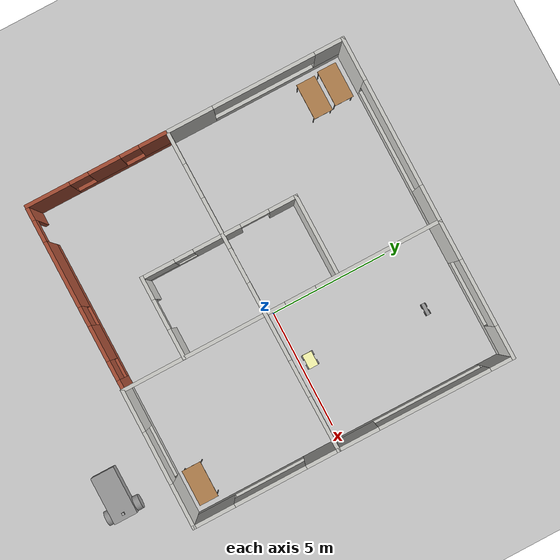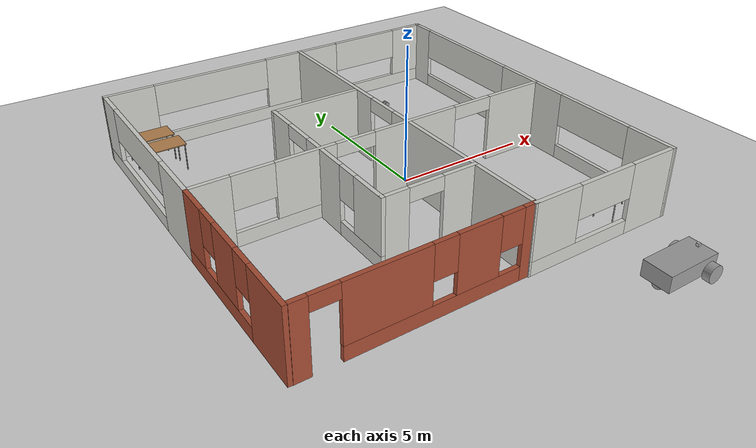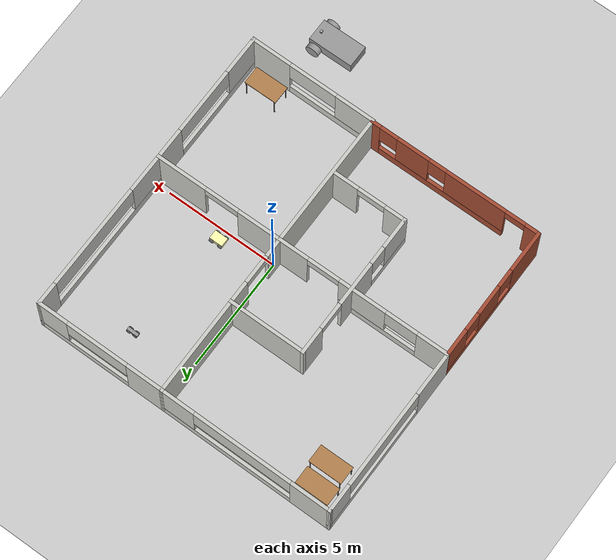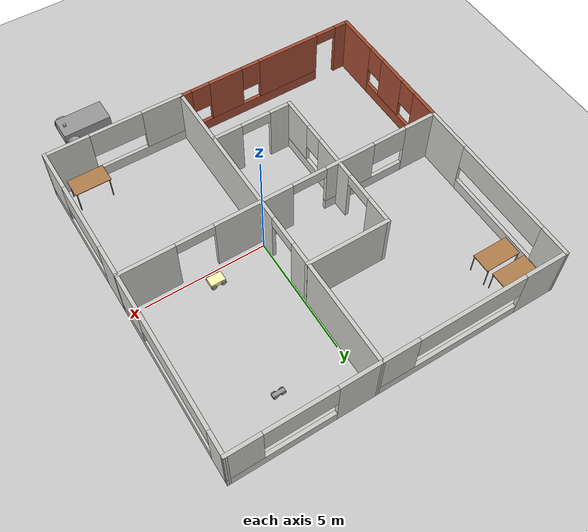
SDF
<sdf version="1.7">
 <world name="default">
  <plugin name="hello" filename="libhello.so"/>
  <light name="sun" type="directional">
   <pose>0 0 10 0 -0 0</pose>
   <diffuse>0.8 0.8 0.8 1</diffuse>
   <specular>0.2 0.2 0.2 1</specular>
   <attenuation>
    <range>1000</range>
    <constant>0.9</constant>
    <linear>0.01</linear>
    <quadratic>0.001</quadratic>
   </attenuation>
   <direction>-0.5 0.1 -0.9</direction>
   <spot><inner_angle>0</inner_angle><outer_angle>0</outer_angle><falloff>0</falloff></spot>
  </light>
  <model name="ground_plane">
   <static>1</static>
   <link name="link">
    <collision name="collision">
     <geometry><plane><normal>0 0 1</normal><size>100 100</size></plane></geometry>
     <surface>
      <contact><collide_bitmask>65535</collide_bitmask></contact>
      <friction><ode><mu>100</mu><mu2>50</mu2></ode></friction>
     </surface>
    </collision>
    <visual name="visual">
     <cast_shadows>0</cast_shadows>
     <geometry><plane><normal>0 0 1</normal><size>100 100</size></plane></geometry>
     <material>
      <script><uri>file://media/materials/scripts/gazebo.material</uri><name>Gazebo/Grey</name></script>
     </material>
    </visual>
   </link>
  </model>
  <gravity>0 0 -9.8</gravity>
  <magnetic_field>6e-06 2.3e-05 -4.2e-05</magnetic_field>
  <atmosphere type="adiabatic"/>
  <physics type="ode">
   <max_step_size>0.001</max_step_size>
   <real_time_factor>1</real_time_factor>
   <real_time_update_rate>1000</real_time_update_rate>
  </physics>
  <scene><ambient>0.4 0.4 0.4 1</ambient><background>0.7 0.7 0.7 1</background><shadows>1</shadows></scene>
  <spherical_coordinates>
   <surface_model>EARTH_WGS84</surface_model>
   <latitude_deg>0</latitude_deg>
   <longitude_deg>0</longitude_deg>
   <elevation>0</elevation>
   <heading_deg>0</heading_deg>
  </spherical_coordinates>
  <model name="floor">
   <pose>-1.1194 0.40926 0 0 -0 0</pose>
   <link name="Wall_0">
    <collision name="Wall_0_Collision">
     <geometry><box><size>3.5 0.15 2.5</size></box></geometry>
     <pose>0 0 1.25 0 -0 0</pose>
    </collision>
    <visual name="Wall_0_Visual">
     <pose>0 0 1.25 0 -0 0</pose>
     <geometry><box><size>3.5 0.15 2.5</size></box></geometry>
     <material>
      <script><uri>file://media/materials/scripts/gazebo.material</uri><name>Gazebo/CeilingTiled</name></script>
      <ambient>0.921569 0.807843 0.615686 1</ambient>
     </material>
     <meta><layer>0</layer></meta>
    </visual>
    <pose>-0.680453 2.40138 0 0 -0 0</pose>
   </link>
   <link name="Wall_10">
    <pose>3.86966 6.71461 0 0 -0 0</pose>
    <visual name="Wall_10_Visual_0">
     <pose>-2.10615 0 1.25 0 -0 0</pose>
     <geometry><box><size>1.71925 0.15 2.5</size></box></geometry>
     <material>
      <script><uri>file://media/materials/scripts/gazebo.material</uri><name>Gazebo/CeilingTiled</name></script>
      <ambient>0.996078 0.47451 0.0196078 1</ambient>
     </material>
     <meta><layer>0</layer></meta>
    </visual>
    <collision name="Wall_10_Collision_0">
     <geometry><box><size>1.71925 0.15 2.5</size></box></geometry>
     <pose>-2.10615 0 1.25 0 -0 0</pose>
    </collision>
    <visual name="Wall_10_Visual_1">
     <pose>0.859627 0 0.25 0 -0 0</pose>
     <geometry><box><size>4.2123 0.15 0.5</size></box></geometry>
     <material>
      <script><uri>file://media/materials/scripts/gazebo.material</uri><name>Gazebo/CeilingTiled</name></script>
      <ambient>0.996078 0.47451 0.0196078 1</ambient>
     </material>
     <meta><layer>0</layer></meta>
    </visual>
    <collision name="Wall_10_Collision_1">
     <geometry><box><size>4.2123 0.15 0.5</size></box></geometry>
     <pose>0.859627 0 0.25 0 -0 0</pose>
    </collision>
    <visual name="Wall_10_Visual_2">
     <pose>2.25525 0 1.5 0 -0 0</pose>
     <geometry><box><size>1.42105 0.15 2</size></box></geometry>
     <material>
      <script><uri>file://media/materials/scripts/gazebo.material</uri><name>Gazebo/CeilingTiled</name></script>
      <ambient>0.996078 0.47451 0.0196078 1</ambient>
     </material>
     <meta><layer>0</layer></meta>
    </visual>
    <collision name="Wall_10_Collision_2">
     <geometry><box><size>1.42105 0.15 2</size></box></geometry>
     <pose>2.25525 0 1.5 0 -0 0</pose>
    </collision>
    <visual name="Wall_10_Visual_3">
     <pose>0.1491 0 1.9 0 -0 0</pose>
     <geometry><box><size>2.79124 0.15 1.2</size></box></geometry>
     <material>
      <script><uri>file://media/materials/scripts/gazebo.material</uri><name>Gazebo/CeilingTiled</name></script>
      <ambient>0.996078 0.47451 0.0196078 1</ambient>
     </material>
     <meta><layer>0</layer></meta>
    </visual>
    <collision name="Wall_10_Collision_3">
     <geometry><box><size>2.79124 0.15 1.2</size></box></geometry>
     <pose>0.1491 0 1.9 0 -0 0</pose>
    </collision>
   </link>
   <link name="Wall_11">
    <pose>6.74514 3.02848 0 0 0 -1.57495</pose>
    <visual name="Wall_11_Visual_0">
     <pose>-3.24419 0 1.25 0 -0 0</pose>
     <geometry><box><size>1.03393 0.15 2.5</size></box></geometry>
     <material>
      <script><uri>file://media/materials/scripts/gazebo.material</uri><name>Gazebo/CeilingTiled</name></script>
      <ambient>0.996078 0.47451 0.0196078 1</ambient>
     </material>
     <meta><layer>0</layer></meta>
    </visual>
    <collision name="Wall_11_Collision_0">
     <geometry><box><size>1.03393 0.15 2.5</size></box></geometry>
     <pose>-3.24419 0 1.25 0 -0 0</pose>
    </collision>
    <visual name="Wall_11_Visual_1">
     <pose>0.516965 0 0.25 0 -0 0</pose>
     <geometry><box><size>6.48838 0.15 0.5</size></box></geometry>
     <material>
      <script><uri>file://media/materials/scripts/gazebo.material</uri><name>Gazebo/CeilingTiled</name></script>
      <ambient>0.996078 0.47451 0.0196078 1</ambient>
     </material>
     <meta><layer>0</layer></meta>
    </visual>
    <collision name="Wall_11_Collision_1">
     <geometry><box><size>6.48838 0.15 0.5</size></box></geometry>
     <pose>0.516965 0 0.25 0 -0 0</pose>
    </collision>
    <visual name="Wall_11_Visual_2">
     <pose>2.86792 0 1.5 0 -0 0</pose>
     <geometry><box><size>1.78646 0.15 2</size></box></geometry>
     <material>
      <script><uri>file://media/materials/scripts/gazebo.material</uri><name>Gazebo/CeilingTiled</name></script>
      <ambient>0.996078 0.47451 0.0196078 1</ambient>
     </material>
     <meta><layer>0</layer></meta>
    </visual>
    <collision name="Wall_11_Collision_2">
     <geometry><box><size>1.78646 0.15 2</size></box></geometry>
     <pose>2.86792 0 1.5 0 -0 0</pose>
    </collision>
    <visual name="Wall_11_Visual_3">
     <pose>-0.376266 0 1.9 0 -0 0</pose>
     <geometry><box><size>4.70192 0.15 1.2</size></box></geometry>
     <material>
      <script><uri>file://media/materials/scripts/gazebo.material</uri><name>Gazebo/CeilingTiled</name></script>
      <ambient>0.996078 0.47451 0.0196078 1</ambient>
     </material>
     <meta><layer>0</layer></meta>
    </visual>
    <collision name="Wall_11_Collision_3">
     <geometry><box><size>4.70192 0.15 1.2</size></box></geometry>
     <pose>-0.376266 0 1.9 0 -0 0</pose>
    </collision>
   </link>
   <link name="Wall_13">
    <pose>-6.76045 3.04378 0 0 -0 1.5708</pose>
    <visual name="Wall_13_Visual_0">
     <pose>-2.80286 0 1.25 0 -0 0</pose>
     <geometry><box><size>1.94712 0.15 2.5</size></box></geometry>
     <material>
      <script><uri>file://media/materials/scripts/gazebo.material</uri><name>Gazebo/CeilingTiled</name></script>
      <ambient>0.996078 0.47451 0.0196078 1</ambient>
     </material>
     <meta><layer>0</layer></meta>
    </visual>
    <collision name="Wall_13_Collision_0">
     <geometry><box><size>1.94712 0.15 2.5</size></box></geometry>
     <pose>-2.80286 0 1.25 0 -0 0</pose>
    </collision>
    <visual name="Wall_13_Visual_1">
     <pose>0.97356 0 0.25 0 -0 0</pose>
     <geometry><box><size>5.60571 0.15 0.5</size></box></geometry>
     <material>
      <script><uri>file://media/materials/scripts/gazebo.material</uri><name>Gazebo/CeilingTiled</name></script>
      <ambient>0.996078 0.47451 0.0196078 1</ambient>
     </material>
     <meta><layer>0</layer></meta>
    </visual>
    <collision name="Wall_13_Collision_1">
     <geometry><box><size>5.60571 0.15 0.5</size></box></geometry>
     <pose>0.97356 0 0.25 0 -0 0</pose>
    </collision>
    <visual name="Wall_13_Visual_2">
     <pose>3.1335 0 1.5 0 -0 0</pose>
     <geometry><box><size>1.28584 0.15 2</size></box></geometry>
     <material>
      <script><uri>file://media/materials/scripts/gazebo.material</uri><name>Gazebo/CeilingTiled</name></script>
      <ambient>0.996078 0.47451 0.0196078 1</ambient>
     </material>
     <meta><layer>0</layer></meta>
    </visual>
    <collision name="Wall_13_Collision_2">
     <geometry><box><size>1.28584 0.15 2</size></box></geometry>
     <pose>3.1335 0 1.5 0 -0 0</pose>
    </collision>
    <visual name="Wall_13_Visual_3">
     <pose>0.330641 0 1.9 0 -0 0</pose>
     <geometry><box><size>4.31987 0.15 1.2</size></box></geometry>
     <material>
      <script><uri>file://media/materials/scripts/gazebo.material</uri><name>Gazebo/CeilingTiled</name></script>
      <ambient>0.996078 0.47451 0.0196078 1</ambient>
     </material>
     <meta><layer>0</layer></meta>
    </visual>
    <collision name="Wall_13_Collision_3">
     <geometry><box><size>4.31987 0.15 1.2</size></box></geometry>
     <pose>0.330641 0 1.9 0 -0 0</pose>
    </collision>
   </link>
   <link name="Wall_14">
    <pose>-2.93667 6.7299 0 0 0 -0.004</pose>
    <visual name="Wall_14_Visual_0">
     <pose>-2.97598 0 1.25 0 -0 0</pose>
     <geometry><box><size>1.84566 0.15 2.5</size></box></geometry>
     <material>
      <script><uri>file://media/materials/scripts/gazebo.material</uri><name>Gazebo/CeilingTiled</name></script>
      <ambient>0.996078 0.47451 0.0196078 1</ambient>
     </material>
     <meta><layer>0</layer></meta>
    </visual>
    <collision name="Wall_14_Collision_0">
     <geometry><box><size>1.84566 0.15 2.5</size></box></geometry>
     <pose>-2.97598 0 1.25 0 -0 0</pose>
    </collision>
    <visual name="Wall_14_Visual_1">
     <pose>0.922833 0 0.25 0 -0 0</pose>
     <geometry><box><size>5.95195 0.15 0.5</size></box></geometry>
     <material>
      <script><uri>file://media/materials/scripts/gazebo.material</uri><name>Gazebo/CeilingTiled</name></script>
      <ambient>0.996078 0.47451 0.0196078 1</ambient>
     </material>
     <meta><layer>0</layer></meta>
    </visual>
    <collision name="Wall_14_Collision_1">
     <geometry><box><size>5.95195 0.15 0.5</size></box></geometry>
     <pose>0.922833 0 0.25 0 -0 0</pose>
    </collision>
    <visual name="Wall_14_Visual_2">
     <pose>3.15291 0 1.5 0 -0 0</pose>
     <geometry><box><size>1.49179 0.15 2</size></box></geometry>
     <material>
      <script><uri>file://media/materials/scripts/gazebo.material</uri><name>Gazebo/CeilingTiled</name></script>
      <ambient>0.996078 0.47451 0.0196078 1</ambient>
     </material>
     <meta><layer>0</layer></meta>
    </visual>
    <collision name="Wall_14_Collision_2">
     <geometry><box><size>1.49179 0.15 2</size></box></geometry>
     <pose>3.15291 0 1.5 0 -0 0</pose>
    </collision>
    <visual name="Wall_14_Visual_3">
     <pose>0.176935 0 1.9 0 -0 0</pose>
     <geometry><box><size>4.46016 0.15 1.2</size></box></geometry>
     <material>
      <script><uri>file://media/materials/scripts/gazebo.material</uri><name>Gazebo/CeilingTiled</name></script>
      <ambient>0.996078 0.47451 0.0196078 1</ambient>
     </material>
     <meta><layer>0</layer></meta>
    </visual>
    <collision name="Wall_14_Collision_3">
     <geometry><box><size>4.46016 0.15 1.2</size></box></geometry>
     <pose>0.176935 0 1.9 0 -0 0</pose>
    </collision>
   </link>
   <link name="Wall_16">
    <pose>-2.35545 -0.856476 0 0 0 -1.5708</pose>
    <visual name="Wall_16_Visual_0">
     <pose>-2.72153 0 1.25 0 -0 0</pose>
     <geometry><box><size>1.22295 0.15 2.5</size></box></geometry>
     <material>
      <script><uri>file://media/materials/scripts/gazebo.material</uri><name>Gazebo/CeilingTiled</name></script>
      <ambient>0.996078 0.47451 0.0196078 1</ambient>
     </material>
     <meta><layer>0</layer></meta>
    </visual>
    <collision name="Wall_16_Collision_0">
     <geometry><box><size>1.22295 0.15 2.5</size></box></geometry>
     <pose>-2.72153 0 1.25 0 -0 0</pose>
    </collision>
    <visual name="Wall_16_Visual_1">
     <pose>0.091031 0 1.25 0 -0 0</pose>
     <geometry><box><size>2.00077 0.15 2.5</size></box></geometry>
     <material>
      <script><uri>file://media/materials/scripts/gazebo.material</uri><name>Gazebo/CeilingTiled</name></script>
      <ambient>0.996078 0.47451 0.0196078 1</ambient>
     </material>
     <meta><layer>0</layer></meta>
    </visual>
    <collision name="Wall_16_Collision_1">
     <geometry><box><size>2.00077 0.15 2.5</size></box></geometry>
     <pose>0.091031 0 1.25 0 -0 0</pose>
    </collision>
    <visual name="Wall_16_Visual_2">
     <pose>2.21221 0 0.25 0 -0 0</pose>
     <geometry><box><size>2.24159 0.15 0.5</size></box></geometry>
     <material>
      <script><uri>file://media/materials/scripts/gazebo.material</uri><name>Gazebo/CeilingTiled</name></script>
      <ambient>0.996078 0.47451 0.0196078 1</ambient>
     </material>
     <meta><layer>0</layer></meta>
    </visual>
    <collision name="Wall_16_Collision_2">
     <geometry><box><size>2.24159 0.15 0.5</size></box></geometry>
     <pose>2.21221 0 0.25 0 -0 0</pose>
    </collision>
    <visual name="Wall_16_Visual_3">
     <pose>2.61221 0 1.5 0 -0 0</pose>
     <geometry><box><size>1.44159 0.15 2</size></box></geometry>
     <material>
      <script><uri>file://media/materials/scripts/gazebo.material</uri><name>Gazebo/CeilingTiled</name></script>
      <ambient>0.996078 0.47451 0.0196078 1</ambient>
     </material>
     <meta><layer>0</layer></meta>
    </visual>
    <collision name="Wall_16_Collision_3">
     <geometry><box><size>1.44159 0.15 2</size></box></geometry>
     <pose>2.61221 0 1.5 0 -0 0</pose>
    </collision>
    <visual name="Wall_16_Visual_4">
     <pose>1.49142 0 1.9 0 -0 0</pose>
     <geometry><box><size>0.8 0.15 1.2</size></box></geometry>
     <material>
      <script><uri>file://media/materials/scripts/gazebo.material</uri><name>Gazebo/CeilingTiled</name></script>
      <ambient>0.996078 0.47451 0.0196078 1</ambient>
     </material>
     <meta><layer>0</layer></meta>
    </visual>
    <collision name="Wall_16_Collision_4">
     <geometry><box><size>0.8 0.15 1.2</size></box></geometry>
     <pose>1.49142 0 1.9 0 -0 0</pose>
    </collision>
    <visual name="Wall_16_Visual_5">
     <pose>-1.5097 0 2.25 0 -0 0</pose>
     <geometry><box><size>1.2007 0.15 0.5</size></box></geometry>
     <material>
      <script><uri>file://media/materials/scripts/gazebo.material</uri><name>Gazebo/CeilingTiled</name></script>
      <ambient>0.996078 0.47451 0.0196078 1</ambient>
     </material>
     <meta><layer>0</layer></meta>
    </visual>
    <collision name="Wall_16_Collision_5">
     <geometry><box><size>1.2007 0.15 0.5</size></box></geometry>
     <pose>-1.5097 0 2.25 0 -0 0</pose>
    </collision>
   </link>
   <link name="Wall_19">
    <pose>-0.680453 -4.11433 0 0 -0 0</pose>
    <visual name="Wall_19_Visual_0">
     <pose>-1.25768 0 1.25 0 -0 0</pose>
     <geometry><box><size>0.984642 0.15 2.5</size></box></geometry>
     <material>
      <script><uri>file://media/materials/scripts/gazebo.material</uri><name>Gazebo/CeilingTiled</name></script>
      <ambient>0.921569 0.807843 0.615686 1</ambient>
     </material>
     <meta><layer>0</layer></meta>
    </visual>
    <collision name="Wall_19_Collision_0">
     <geometry><box><size>0.984642 0.15 2.5</size></box></geometry>
     <pose>-1.25768 0 1.25 0 -0 0</pose>
    </collision>
    <visual name="Wall_19_Visual_1">
     <pose>1.1158 0 1.25 0 -0 0</pose>
     <geometry><box><size>1.2684 0.15 2.5</size></box></geometry>
     <material>
      <script><uri>file://media/materials/scripts/gazebo.material</uri><name>Gazebo/CeilingTiled</name></script>
      <ambient>0.921569 0.807843 0.615686 1</ambient>
     </material>
     <meta><layer>0</layer></meta>
    </visual>
    <collision name="Wall_19_Collision_1">
     <geometry><box><size>1.2684 0.15 2.5</size></box></geometry>
     <pose>1.1158 0 1.25 0 -0 0</pose>
    </collision>
    <visual name="Wall_19_Visual_2">
     <pose>-0.141879 0 2.25 0 -0 0</pose>
     <geometry><box><size>1.24696 0.15 0.5</size></box></geometry>
     <material>
      <script><uri>file://media/materials/scripts/gazebo.material</uri><name>Gazebo/CeilingTiled</name></script>
      <ambient>0.921569 0.807843 0.615686 1</ambient>
     </material>
     <meta><layer>0</layer></meta>
    </visual>
    <collision name="Wall_19_Collision_2">
     <geometry><box><size>1.24696 0.15 0.5</size></box></geometry>
     <pose>-0.141879 0 2.25 0 -0 0</pose>
    </collision>
   </link>
   <link name="Wall_6">
    <pose>-5e-06 -0.68823 0 0 -0 0.004545</pose>
    <visual name="Wall_6_Visual_0">
     <pose>-6.09809 0 1.25 0 -0 0</pose>
     <geometry><box><size>1.41365 0.15 2.5</size></box></geometry>
     <material>
      <script><uri>file://media/materials/scripts/gazebo.material</uri><name>Gazebo/CeilingTiled</name></script>
      <ambient>0.921569 0.807843 0.615686 1</ambient>
     </material>
     <meta><layer>0</layer></meta>
    </visual>
    <collision name="Wall_6_Collision_0">
     <geometry><box><size>1.41365 0.15 2.5</size></box></geometry>
     <pose>-6.09809 0 1.25 0 -0 0</pose>
    </collision>
    <visual name="Wall_6_Visual_1">
     <pose>1.30078 0 1.25 0 -0 0</pose>
     <geometry><box><size>3.27649 0.15 2.5</size></box></geometry>
     <material>
      <script><uri>file://media/materials/scripts/gazebo.material</uri><name>Gazebo/CeilingTiled</name></script>
      <ambient>0.921569 0.807843 0.615686 1</ambient>
     </material>
     <meta><layer>0</layer></meta>
    </visual>
    <collision name="Wall_6_Collision_1">
     <geometry><box><size>3.27649 0.15 2.5</size></box></geometry>
     <pose>1.30078 0 1.25 0 -0 0</pose>
    </collision>
    <visual name="Wall_6_Visual_2">
     <pose>5.64099 0 1.25 0 -0 0</pose>
     <geometry><box><size>2.32786 0.15 2.5</size></box></geometry>
     <material>
      <script><uri>file://media/materials/scripts/gazebo.material</uri><name>Gazebo/CeilingTiled</name></script>
      <ambient>0.921569 0.807843 0.615686 1</ambient>
     </material>
     <meta><layer>0</layer></meta>
    </visual>
    <collision name="Wall_6_Collision_2">
     <geometry><box><size>2.32786 0.15 2.5</size></box></geometry>
     <pose>5.64099 0 1.25 0 -0 0</pose>
    </collision>
    <visual name="Wall_6_Visual_3">
     <pose>-3.59193 0 0.25 0 -0 0</pose>
     <geometry><box><size>3.59867 0.15 0.5</size></box></geometry>
     <material>
      <script><uri>file://media/materials/scripts/gazebo.material</uri><name>Gazebo/CeilingTiled</name></script>
      <ambient>0.921569 0.807843 0.615686 1</ambient>
     </material>
     <meta><layer>0</layer></meta>
    </visual>
    <collision name="Wall_6_Collision_3">
     <geometry><box><size>3.59867 0.15 0.5</size></box></geometry>
     <pose>-3.59193 0 0.25 0 -0 0</pose>
    </collision>
    <visual name="Wall_6_Visual_4">
     <pose>-2.86816 0 1.5 0 -0 0</pose>
     <geometry><box><size>2.15113 0.15 2</size></box></geometry>
     <material>
      <script><uri>file://media/materials/scripts/gazebo.material</uri><name>Gazebo/CeilingTiled</name></script>
      <ambient>0.921569 0.807843 0.615686 1</ambient>
     </material>
     <meta><layer>0</layer></meta>
    </visual>
    <collision name="Wall_6_Collision_4">
     <geometry><box><size>2.15113 0.15 2</size></box></geometry>
     <pose>-2.86816 0 1.5 0 -0 0</pose>
    </collision>
    <visual name="Wall_6_Visual_5">
     <pose>-4.6675 0 1.9 0 -0 0</pose>
     <geometry><box><size>1.44755 0.15 1.2</size></box></geometry>
     <material>
      <script><uri>file://media/materials/scripts/gazebo.material</uri><name>Gazebo/CeilingTiled</name></script>
      <ambient>0.921569 0.807843 0.615686 1</ambient>
     </material>
     <meta><layer>0</layer></meta>
    </visual>
    <collision name="Wall_6_Collision_5">
     <geometry><box><size>1.44755 0.15 1.2</size></box></geometry>
     <pose>-4.6675 0 1.9 0 -0 0</pose>
    </collision>
    <visual name="Wall_6_Visual_6">
     <pose>3.70804 0 2.25 0 -0 0</pose>
     <geometry><box><size>1.53804 0.15 0.5</size></box></geometry>
     <material>
      <script><uri>file://media/materials/scripts/gazebo.material</uri><name>Gazebo/CeilingTiled</name></script>
      <ambient>0.921569 0.807843 0.615686 1</ambient>
     </material>
     <meta><layer>0</layer></meta>
    </visual>
    <collision name="Wall_6_Collision_6">
     <geometry><box><size>1.53804 0.15 0.5</size></box></geometry>
     <pose>3.70804 0 2.25 0 -0 0</pose>
    </collision>
    <visual name="Wall_6_Visual_7">
     <pose>-1.06503 0 2.25 0 -0 0</pose>
     <geometry><box><size>1.45513 0.15 0.5</size></box></geometry>
     <material>
      <script><uri>file://media/materials/scripts/gazebo.material</uri><name>Gazebo/CeilingTiled</name></script>
      <ambient>0.921569 0.807843 0.615686 1</ambient>
     </material>
     <meta><layer>0</layer></meta>
    </visual>
    <collision name="Wall_6_Collision_7">
     <geometry><box><size>1.45513 0.15 0.5</size></box></geometry>
     <pose>-1.06503 0 2.25 0 -0 0</pose>
    </collision>
   </link>
   <link name="Wall_7">
    <pose>6.72985 -3.70137 0 0 0 -1.5708</pose>
    <visual name="Wall_7_Visual_0">
     <pose>-2.40595 0 1.25 0 -0 0</pose>
     <geometry><box><size>1.42563 0.15 2.5</size></box></geometry>
     <material>
      <script><uri>file://media/materials/scripts/gazebo.material</uri><name>Gazebo/CeilingTiled</name></script>
      <ambient>0.996078 0.47451 0.0196078 1</ambient>
     </material>
     <meta><layer>0</layer></meta>
    </visual>
    <collision name="Wall_7_Collision_0">
     <geometry><box><size>1.42563 0.15 2.5</size></box></geometry>
     <pose>-2.40595 0 1.25 0 -0 0</pose>
    </collision>
    <visual name="Wall_7_Visual_1">
     <pose>0.712816 0 0.25 0 -0 0</pose>
     <geometry><box><size>4.8119 0.15 0.5</size></box></geometry>
     <material>
      <script><uri>file://media/materials/scripts/gazebo.material</uri><name>Gazebo/CeilingTiled</name></script>
      <ambient>0.996078 0.47451 0.0196078 1</ambient>
     </material>
     <meta><layer>0</layer></meta>
    </visual>
    <collision name="Wall_7_Collision_1">
     <geometry><box><size>4.8119 0.15 0.5</size></box></geometry>
     <pose>0.712816 0 0.25 0 -0 0</pose>
    </collision>
    <visual name="Wall_7_Visual_2">
     <pose>2.21906 0 1.5 0 -0 0</pose>
     <geometry><box><size>1.79941 0.15 2</size></box></geometry>
     <material>
      <script><uri>file://media/materials/scripts/gazebo.material</uri><name>Gazebo/CeilingTiled</name></script>
      <ambient>0.996078 0.47451 0.0196078 1</ambient>
     </material>
     <meta><layer>0</layer></meta>
    </visual>
    <collision name="Wall_7_Collision_2">
     <geometry><box><size>1.79941 0.15 2</size></box></geometry>
     <pose>2.21906 0 1.5 0 -0 0</pose>
    </collision>
    <visual name="Wall_7_Visual_3">
     <pose>-0.186888 0 1.9 0 -0 0</pose>
     <geometry><box><size>3.01249 0.15 1.2</size></box></geometry>
     <material>
      <script><uri>file://media/materials/scripts/gazebo.material</uri><name>Gazebo/CeilingTiled</name></script>
      <ambient>0.996078 0.47451 0.0196078 1</ambient>
     </material>
     <meta><layer>0</layer></meta>
    </visual>
    <collision name="Wall_7_Collision_3">
     <geometry><box><size>3.01249 0.15 1.2</size></box></geometry>
     <pose>-0.186888 0 1.9 0 -0 0</pose>
    </collision>
   </link>
   <link name="Wall_8">
    <pose>3.86966 -6.7298 0 0 -0 3.13625</pose>
    <visual name="Wall_8_Visual_0">
     <pose>-1.99488 0 1.25 0 -0 0</pose>
     <geometry><box><size>1.8807 0.15 2.5</size></box></geometry>
     <material>
      <script><uri>file://media/materials/scripts/gazebo.material</uri><name>Gazebo/CeilingTiled</name></script>
      <ambient>0.996078 0.47451 0.0196078 1</ambient>
     </material>
     <meta><layer>0</layer></meta>
    </visual>
    <collision name="Wall_8_Collision_0">
     <geometry><box><size>1.8807 0.15 2.5</size></box></geometry>
     <pose>-1.99488 0 1.25 0 -0 0</pose>
    </collision>
    <visual name="Wall_8_Visual_1">
     <pose>0.940351 0 0.25 0 -0 0</pose>
     <geometry><box><size>3.98975 0.15 0.5</size></box></geometry>
     <material>
      <script><uri>file://media/materials/scripts/gazebo.material</uri><name>Gazebo/CeilingTiled</name></script>
      <ambient>0.996078 0.47451 0.0196078 1</ambient>
     </material>
     <meta><layer>0</layer></meta>
    </visual>
    <collision name="Wall_8_Collision_1">
     <geometry><box><size>3.98975 0.15 0.5</size></box></geometry>
     <pose>0.940351 0 0.25 0 -0 0</pose>
    </collision>
    <visual name="Wall_8_Visual_2">
     <pose>2.03431 0 1.5 0 -0 0</pose>
     <geometry><box><size>1.80183 0.15 2</size></box></geometry>
     <material>
      <script><uri>file://media/materials/scripts/gazebo.material</uri><name>Gazebo/CeilingTiled</name></script>
      <ambient>0.996078 0.47451 0.0196078 1</ambient>
     </material>
     <meta><layer>0</layer></meta>
    </visual>
    <collision name="Wall_8_Collision_2">
     <geometry><box><size>1.80183 0.15 2</size></box></geometry>
     <pose>2.03431 0 1.5 0 -0 0</pose>
    </collision>
    <visual name="Wall_8_Visual_3">
     <pose>0.039436 0 1.9 0 -0 0</pose>
     <geometry><box><size>2.18792 0.15 1.2</size></box></geometry>
     <material>
      <script><uri>file://media/materials/scripts/gazebo.material</uri><name>Gazebo/CeilingTiled</name></script>
      <ambient>0.996078 0.47451 0.0196078 1</ambient>
     </material>
     <meta><layer>0</layer></meta>
    </visual>
    <collision name="Wall_8_Collision_3">
     <geometry><box><size>2.18792 0.15 1.2</size></box></geometry>
     <pose>0.039436 0 1.9 0 -0 0</pose>
    </collision>
   </link>
   <link name="Wall_9">
    <pose>0.994177 5e-05 0 0 -0 1.57307</pose>
    <visual name="Wall_9_Visual_0">
     <pose>-3.31645 0 1.25 0 -0 0</pose>
     <geometry><box><size>6.94625 0.15 2.5</size></box></geometry>
     <material>
      <script><uri>file://media/materials/scripts/gazebo.material</uri><name>Gazebo/CeilingTiled</name></script>
      <ambient>0.921569 0.807843 0.615686 1</ambient>
     </material>
     <meta><layer>0</layer></meta>
    </visual>
    <collision name="Wall_9_Collision_0">
     <geometry><box><size>6.94625 0.15 2.5</size></box></geometry>
     <pose>-3.31645 0 1.25 0 -0 0</pose>
    </collision>
    <visual name="Wall_9_Visual_1">
     <pose>4.11974 0 1.25 0 -0 0</pose>
     <geometry><box><size>5.33967 0.15 2.5</size></box></geometry>
     <material>
      <script><uri>file://media/materials/scripts/gazebo.material</uri><name>Gazebo/CeilingTiled</name></script>
      <ambient>0.921569 0.807843 0.615686 1</ambient>
     </material>
     <meta><layer>0</layer></meta>
    </visual>
    <collision name="Wall_9_Collision_1">
     <geometry><box><size>5.33967 0.15 2.5</size></box></geometry>
     <pose>4.11974 0 1.25 0 -0 0</pose>
    </collision>
    <visual name="Wall_9_Visual_2">
     <pose>0.803289 0 2.25 0 -0 0</pose>
     <geometry><box><size>1.29322 0.15 0.5</size></box></geometry>
     <material>
      <script><uri>file://media/materials/scripts/gazebo.material</uri><name>Gazebo/CeilingTiled</name></script>
      <ambient>0.921569 0.807843 0.615686 1</ambient>
     </material>
     <meta><layer>0</layer></meta>
    </visual>
    <collision name="Wall_9_Collision_2">
     <geometry><box><size>1.29322 0.15 0.5</size></box></geometry>
     <pose>0.803289 0 2.25 0 -0 0</pose>
    </collision>
   </link>
   <static>1</static>
  </model>
  <model name="table">
   <static>1</static>
   <link name="link">
    <collision name="surface">
     <pose>0 0 1 0 -0 0</pose>
     <geometry><box><size>1.5 0.8 0.03</size></box></geometry>
     <surface><friction><ode><mu>0.6</mu><mu2>0.6</mu2></ode></friction></surface>
    </collision>
    <visual name="visual1">
     <pose>0 0 1 0 -0 0</pose>
     <geometry><box><size>1.5 0.8 0.03</size></box></geometry>
     <material>
      <script><uri>file://media/materials/scripts/gazebo.material</uri><name>Gazebo/Wood</name></script>
     </material>
    </visual>
    <collision name="front_left_leg">
     <pose>0.68 0.38 0.5 0 -0 0</pose>
     <geometry><cylinder><radius>0.02</radius><length>1</length></cylinder></geometry>
    </collision>
    <visual name="front_left_leg">
     <pose>0.68 0.38 0.5 0 -0 0</pose>
     <geometry><cylinder><radius>0.02</radius><length>1</length></cylinder></geometry>
     <material>
      <script><uri>file://media/materials/scripts/gazebo.material</uri><name>Gazebo/Grey</name></script>
     </material>
    </visual>
    <collision name="front_right_leg">
     <pose>0.68 -0.38 0.5 0 -0 0</pose>
     <geometry><cylinder><radius>0.02</radius><length>1</length></cylinder></geometry>
    </collision>
    <visual name="front_right_leg">
     <pose>0.68 -0.38 0.5 0 -0 0</pose>
     <geometry><cylinder><radius>0.02</radius><length>1</length></cylinder></geometry>
     <material>
      <script><uri>file://media/materials/scripts/gazebo.material</uri><name>Gazebo/Grey</name></script>
     </material>
    </visual>
    <collision name="back_right_leg">
     <pose>-0.68 -0.38 0.5 0 -0 0</pose>
     <geometry><cylinder><radius>0.02</radius><length>1</length></cylinder></geometry>
    </collision>
    <visual name="back_right_leg">
     <pose>-0.68 -0.38 0.5 0 -0 0</pose>
     <geometry><cylinder><radius>0.02</radius><length>1</length></cylinder></geometry>
     <material>
      <script><uri>file://media/materials/scripts/gazebo.material</uri><name>Gazebo/Grey</name></script>
     </material>
    </visual>
    <collision name="back_left_leg">
     <pose>-0.68 0.38 0.5 0 -0 0</pose>
     <geometry><cylinder><radius>0.02</radius><length>1</length></cylinder></geometry>
    </collision>
    <visual name="back_left_leg">
     <pose>-0.68 0.38 0.5 0 -0 0</pose>
     <geometry><cylinder><radius>0.02</radius><length>1</length></cylinder></geometry>
     <material>
      <script><uri>file://media/materials/scripts/gazebo.material</uri><name>Gazebo/Grey</name></script>
     </material>
    </visual>
   </link>
   <pose>-6.73396 6.32462 0 0 -0 0</pose>
  </model>
  <model name="table_clone">
   <static>1</static>
   <link name="link">
    <collision name="surface">
     <pose>0 0 1 0 -0 0</pose>
     <geometry><box><size>1.5 0.8 0.03</size></box></geometry>
     <surface><friction><ode><mu>0.6</mu><mu2>0.6</mu2></ode></friction></surface>
    </collision>
    <visual name="visual1">
     <pose>0 0 1 0 -0 0</pose>
     <geometry><box><size>1.5 0.8 0.03</size></box></geometry>
     <material>
      <script><uri>file://media/materials/scripts/gazebo.material</uri><name>Gazebo/Wood</name></script>
     </material>
    </visual>
    <collision name="front_left_leg">
     <pose>0.68 0.38 0.5 0 -0 0</pose>
     <geometry><cylinder><radius>0.02</radius><length>1</length></cylinder></geometry>
    </collision>
    <visual name="front_left_leg">
     <pose>0.68 0.38 0.5 0 -0 0</pose>
     <geometry><cylinder><radius>0.02</radius><length>1</length></cylinder></geometry>
     <material>
      <script><uri>file://media/materials/scripts/gazebo.material</uri><name>Gazebo/Grey</name></script>
     </material>
    </visual>
    <collision name="front_right_leg">
     <pose>0.68 -0.38 0.5 0 -0 0</pose>
     <geometry><cylinder><radius>0.02</radius><length>1</length></cylinder></geometry>
    </collision>
    <visual name="front_right_leg">
     <pose>0.68 -0.38 0.5 0 -0 0</pose>
     <geometry><cylinder><radius>0.02</radius><length>1</length></cylinder></geometry>
     <material>
      <script><uri>file://media/materials/scripts/gazebo.material</uri><name>Gazebo/Grey</name></script>
     </material>
    </visual>
    <collision name="back_right_leg">
     <pose>-0.68 -0.38 0.5 0 -0 0</pose>
     <geometry><cylinder><radius>0.02</radius><length>1</length></cylinder></geometry>
    </collision>
    <visual name="back_right_leg">
     <pose>-0.68 -0.38 0.5 0 -0 0</pose>
     <geometry><cylinder><radius>0.02</radius><length>1</length></cylinder></geometry>
     <material>
      <script><uri>file://media/materials/scripts/gazebo.material</uri><name>Gazebo/Grey</name></script>
     </material>
    </visual>
    <collision name="back_left_leg">
     <pose>-0.68 0.38 0.5 0 -0 0</pose>
     <geometry><cylinder><radius>0.02</radius><length>1</length></cylinder></geometry>
    </collision>
    <visual name="back_left_leg">
     <pose>-0.68 0.38 0.5 0 -0 0</pose>
     <geometry><cylinder><radius>0.02</radius><length>1</length></cylinder></geometry>
     <material>
      <script><uri>file://media/materials/scripts/gazebo.material</uri><name>Gazebo/Grey</name></script>
     </material>
    </visual>
   </link>
   <pose>-6.6553 5.36265 0 0 -0 0</pose>
  </model>
  <model name="table_clone_0">
   <static>1</static>
   <link name="link">
    <collision name="surface">
     <pose>0 0 1 0 -0 0</pose>
     <geometry><box><size>1.5 0.8 0.03</size></box></geometry>
     <surface><friction><ode><mu>0.6</mu><mu2>0.6</mu2></ode></friction></surface>
    </collision>
    <visual name="visual1">
     <pose>0 0 1 0 -0 0</pose>
     <geometry><box><size>1.5 0.8 0.03</size></box></geometry>
     <material>
      <script><uri>file://media/materials/scripts/gazebo.material</uri><name>Gazebo/Wood</name></script>
     </material>
    </visual>
    <collision name="front_left_leg">
     <pose>0.68 0.38 0.5 0 -0 0</pose>
     <geometry><cylinder><radius>0.02</radius><length>1</length></cylinder></geometry>
    </collision>
    <visual name="front_left_leg">
     <pose>0.68 0.38 0.5 0 -0 0</pose>
     <geometry><cylinder><radius>0.02</radius><length>1</length></cylinder></geometry>
     <material>
      <script><uri>file://media/materials/scripts/gazebo.material</uri><name>Gazebo/Grey</name></script>
     </material>
    </visual>
    <collision name="front_right_leg">
     <pose>0.68 -0.38 0.5 0 -0 0</pose>
     <geometry><cylinder><radius>0.02</radius><length>1</length></cylinder></geometry>
    </collision>
    <visual name="front_right_leg">
     <pose>0.68 -0.38 0.5 0 -0 0</pose>
     <geometry><cylinder><radius>0.02</radius><length>1</length></cylinder></geometry>
     <material>
      <script><uri>file://media/materials/scripts/gazebo.material</uri><name>Gazebo/Grey</name></script>
     </material>
    </visual>
    <collision name="back_right_leg">
     <pose>-0.68 -0.38 0.5 0 -0 0</pose>
     <geometry><cylinder><radius>0.02</radius><length>1</length></cylinder></geometry>
    </collision>
    <visual name="back_right_leg">
     <pose>-0.68 -0.38 0.5 0 -0 0</pose>
     <geometry><cylinder><radius>0.02</radius><length>1</length></cylinder></geometry>
     <material>
      <script><uri>file://media/materials/scripts/gazebo.material</uri><name>Gazebo/Grey</name></script>
     </material>
    </visual>
    <collision name="back_left_leg">
     <pose>-0.68 0.38 0.5 0 -0 0</pose>
     <geometry><cylinder><radius>0.02</radius><length>1</length></cylinder></geometry>
    </collision>
    <visual name="back_left_leg">
     <pose>-0.68 0.38 0.5 0 -0 0</pose>
     <geometry><cylinder><radius>0.02</radius><length>1</length></cylinder></geometry>
     <material>
      <script><uri>file://media/materials/scripts/gazebo.material</uri><name>Gazebo/Grey</name></script>
     </material>
    </visual>
   </link>
   <pose>4.45347 -5.56698 0 0 -0 0</pose>
  </model>
  <model name="vehicleRobot">
   <link name="link_3">
    <pose>0 -0.0017 0 0 -0 0</pose>
    <inertial>
     <mass>1</mass>
     <inertia>
      <ixx>0.166667</ixx>
      <ixy>0</ixy>
      <ixz>0</ixz>
      <iyy>0.166667</iyy>
      <iyz>0</iyz>
      <izz>0.166667</izz>
     </inertia>
    </inertial>
    <visual name="visual">
     <geometry><box><size>0.5 0.15 0.1</size></box></geometry>
     <material>
      <lighting>1</lighting>
      <script><uri>file://media/materials/scripts/gazebo.material</uri><name>Gazebo/Grey</name></script>
      <shader type="pixel"><normal_map>__default__</normal_map></shader>
      <ambient>0.3 0.3 0.3 1</ambient>
      <diffuse>0.7 0.7 0.7 1</diffuse>
      <specular>0.01 0.01 0.01 1</specular>
      <emissive>0 0 0 1</emissive>
     </material>
    </visual>
    <collision name="collision">
     <geometry><box><size>0.5 0.15 0.1</size></box></geometry>
     <surface>
      <friction>
       <ode><mu>1</mu><mu2>1</mu2><fdir1>0 0 0</fdir1><slip1>0</slip1><slip2>0</slip2></ode>
       <torsional>
        <coefficient>1</coefficient>
        <patch_radius>0</patch_radius>
        <surface_radius>0</surface_radius>
        <use_patch_radius>1</use_patch_radius>
        <ode><slip>0</slip></ode>
       </torsional>
      </friction>
      <bounce><restitution_coefficient>0</restitution_coefficient><threshold>1e+06</threshold></bounce>
      <contact>
       <collide_without_contact>0</collide_without_contact>
       <collide_without_contact_bitmask>1</collide_without_contact_bitmask>
       <collide_bitmask>1</collide_bitmask>
       <ode>
        <soft_cfm>0</soft_cfm>
        <soft_erp>0.2</soft_erp>
        <kp>1e+13</kp>
        <kd>1</kd>
        <max_vel>0.01</max_vel>
        <min_depth>0</min_depth>
       </ode>
       <bullet>
        <split_impulse>1</split_impulse>
        <split_impulse_penetration_threshold>-0.01</split_impulse_penetration_threshold>
        <soft_cfm>0</soft_cfm>
        <soft_erp>0.2</soft_erp>
        <kp>1e+13</kp>
        <kd>1</kd>
       </bullet>
      </contact>
     </surface>
    </collision>
   </link>
   <link name="link_4_clone">
    <pose>-0.15 -0.0917 0 1.5708 -0 0</pose>
    <inertial>
     <mass>1</mass>
     <inertia><ixx>0.145833</ixx><ixy>0</ixy><ixz>0</ixz><iyy>0.145833</iyy><iyz>0</iyz><izz>0.125</izz></inertia>
    </inertial>
    <visual name="visual">
     <geometry><cylinder><radius>0.1</radius><length>0.03</length></cylinder></geometry>
     <material>
      <lighting>1</lighting>
      <script><uri>file://media/materials/scripts/gazebo.material</uri><name>Gazebo/Grey</name></script>
      <shader type="pixel"><normal_map>__default__</normal_map></shader>
      <ambient>0.3 0.3 0.3 1</ambient>
      <diffuse>0.7 0.7 0.7 1</diffuse>
      <specular>0.01 0.01 0.01 1</specular>
      <emissive>0 0 0 1</emissive>
     </material>
    </visual>
    <collision name="collision">
     <geometry><cylinder><radius>0.1</radius><length>0.03</length></cylinder></geometry>
     <surface>
      <friction>
       <ode><mu>1</mu><mu2>1</mu2><fdir1>0 0 0</fdir1><slip1>0</slip1><slip2>0</slip2></ode>
       <torsional>
        <coefficient>1</coefficient>
        <patch_radius>0</patch_radius>
        <surface_radius>0</surface_radius>
        <use_patch_radius>1</use_patch_radius>
        <ode><slip>0</slip></ode>
       </torsional>
      </friction>
      <bounce><restitution_coefficient>0</restitution_coefficient><threshold>1e+06</threshold></bounce>
      <contact>
       <collide_without_contact>0</collide_without_contact>
       <collide_without_contact_bitmask>1</collide_without_contact_bitmask>
       <collide_bitmask>1</collide_bitmask>
       <ode>
        <soft_cfm>0</soft_cfm>
        <soft_erp>0.2</soft_erp>
        <kp>1e+13</kp>
        <kd>1</kd>
        <max_vel>0.01</max_vel>
        <min_depth>0</min_depth>
       </ode>
       <bullet>
        <split_impulse>1</split_impulse>
        <split_impulse_penetration_threshold>-0.01</split_impulse_penetration_threshold>
        <soft_cfm>0</soft_cfm>
        <soft_erp>0.2</soft_erp>
        <kp>1e+13</kp>
        <kd>1</kd>
       </bullet>
      </contact>
     </surface>
    </collision>
   </link>
   <link name="link_4_clone_0">
    <pose>0.15 -0.0917 -0 1.5708 -0 0</pose>
    <inertial>
     <mass>1</mass>
     <inertia><ixx>0.145833</ixx><ixy>0</ixy><ixz>0</ixz><iyy>0.145833</iyy><iyz>0</iyz><izz>0.125</izz></inertia>
    </inertial>
    <visual name="visual">
     <geometry><cylinder><radius>0.1</radius><length>0.03</length></cylinder></geometry>
     <material>
      <lighting>1</lighting>
      <script><uri>file://media/materials/scripts/gazebo.material</uri><name>Gazebo/Grey</name></script>
      <shader type="pixel"><normal_map>__default__</normal_map></shader>
      <ambient>0.3 0.3 0.3 1</ambient>
      <diffuse>0.7 0.7 0.7 1</diffuse>
      <specular>0.01 0.01 0.01 1</specular>
      <emissive>0 0 0 1</emissive>
     </material>
    </visual>
    <collision name="collision">
     <geometry><cylinder><radius>0.1</radius><length>0.03</length></cylinder></geometry>
     <surface>
      <friction>
       <ode><mu>1</mu><mu2>1</mu2><fdir1>0 0 0</fdir1><slip1>0</slip1><slip2>0</slip2></ode>
       <torsional>
        <coefficient>1</coefficient>
        <patch_radius>0</patch_radius>
        <surface_radius>0</surface_radius>
        <use_patch_radius>1</use_patch_radius>
        <ode><slip>0</slip></ode>
       </torsional>
      </friction>
      <bounce><restitution_coefficient>0</restitution_coefficient><threshold>1e+06</threshold></bounce>
      <contact>
       <collide_without_contact>0</collide_without_contact>
       <collide_without_contact_bitmask>1</collide_without_contact_bitmask>
       <collide_bitmask>1</collide_bitmask>
       <ode>
        <soft_cfm>0</soft_cfm>
        <soft_erp>0.2</soft_erp>
        <kp>1e+13</kp>
        <kd>1</kd>
        <max_vel>0.01</max_vel>
        <min_depth>0</min_depth>
       </ode>
       <bullet>
        <split_impulse>1</split_impulse>
        <split_impulse_penetration_threshold>-0.01</split_impulse_penetration_threshold>
        <soft_cfm>0</soft_cfm>
        <soft_erp>0.2</soft_erp>
        <kp>1e+13</kp>
        <kd>1</kd>
       </bullet>
      </contact>
     </surface>
    </collision>
   </link>
   <link name="link_4_clone_1">
    <pose>-0.15 0.09255 0 1.5708 -0 0</pose>
    <inertial>
     <mass>1</mass>
     <inertia><ixx>0.145833</ixx><ixy>0</ixy><ixz>0</ixz><iyy>0.145833</iyy><iyz>0</iyz><izz>0.125</izz></inertia>
    </inertial>
    <visual name="visual">
     <geometry><cylinder><radius>0.1</radius><length>0.03</length></cylinder></geometry>
     <material>
      <lighting>1</lighting>
      <script><uri>file://media/materials/scripts/gazebo.material</uri><name>Gazebo/Grey</name></script>
      <shader type="pixel"><normal_map>__default__</normal_map></shader>
      <ambient>0.3 0.3 0.3 1</ambient>
      <diffuse>0.7 0.7 0.7 1</diffuse>
      <specular>0.01 0.01 0.01 1</specular>
      <emissive>0 0 0 1</emissive>
     </material>
    </visual>
    <collision name="collision">
     <geometry><cylinder><radius>0.1</radius><length>0.03</length></cylinder></geometry>
     <surface>
      <friction>
       <ode><mu>1</mu><mu2>1</mu2><fdir1>0 0 0</fdir1><slip1>0</slip1><slip2>0</slip2></ode>
       <torsional>
        <coefficient>1</coefficient>
        <patch_radius>0</patch_radius>
        <surface_radius>0</surface_radius>
        <use_patch_radius>1</use_patch_radius>
        <ode><slip>0</slip></ode>
       </torsional>
      </friction>
      <bounce><restitution_coefficient>0</restitution_coefficient><threshold>1e+06</threshold></bounce>
      <contact>
       <collide_without_contact>0</collide_without_contact>
       <collide_without_contact_bitmask>1</collide_without_contact_bitmask>
       <collide_bitmask>1</collide_bitmask>
       <ode>
        <soft_cfm>0</soft_cfm>
        <soft_erp>0.2</soft_erp>
        <kp>1e+13</kp>
        <kd>1</kd>
        <max_vel>0.01</max_vel>
        <min_depth>0</min_depth>
       </ode>
       <bullet>
        <split_impulse>1</split_impulse>
        <split_impulse_penetration_threshold>-0.01</split_impulse_penetration_threshold>
        <soft_cfm>0</soft_cfm>
        <soft_erp>0.2</soft_erp>
        <kp>1e+13</kp>
        <kd>1</kd>
       </bullet>
      </contact>
     </surface>
    </collision>
   </link>
   <link name="link_4_clone_1_clone">
    <pose>0.15 0.09255 0 1.5708 -0 0</pose>
    <inertial>
     <mass>1</mass>
     <inertia><ixx>0.145833</ixx><ixy>0</ixy><ixz>0</ixz><iyy>0.145833</iyy><iyz>0</iyz><izz>0.125</izz></inertia>
    </inertial>
    <visual name="visual">
     <geometry><cylinder><radius>0.1</radius><length>0.03</length></cylinder></geometry>
     <material>
      <lighting>1</lighting>
      <script><uri>file://media/materials/scripts/gazebo.material</uri><name>Gazebo/Grey</name></script>
      <shader type="pixel"><normal_map>__default__</normal_map></shader>
      <ambient>0.3 0.3 0.3 1</ambient>
      <diffuse>0.7 0.7 0.7 1</diffuse>
      <specular>0.01 0.01 0.01 1</specular>
      <emissive>0 0 0 1</emissive>
     </material>
    </visual>
    <collision name="collision">
     <geometry><cylinder><radius>0.1</radius><length>0.03</length></cylinder></geometry>
     <surface>
      <friction>
       <ode><mu>1</mu><mu2>1</mu2><fdir1>0 0 0</fdir1><slip1>0</slip1><slip2>0</slip2></ode>
       <torsional>
        <coefficient>1</coefficient>
        <patch_radius>0</patch_radius>
        <surface_radius>0</surface_radius>
        <use_patch_radius>1</use_patch_radius>
        <ode><slip>0</slip></ode>
       </torsional>
      </friction>
      <bounce><restitution_coefficient>0</restitution_coefficient><threshold>1e+06</threshold></bounce>
      <contact>
       <collide_without_contact>0</collide_without_contact>
       <collide_without_contact_bitmask>1</collide_without_contact_bitmask>
       <collide_bitmask>1</collide_bitmask>
       <ode>
        <soft_cfm>0</soft_cfm>
        <soft_erp>0.2</soft_erp>
        <kp>1e+13</kp>
        <kd>1</kd>
        <max_vel>0.01</max_vel>
        <min_depth>0</min_depth>
       </ode>
       <bullet>
        <split_impulse>1</split_impulse>
        <split_impulse_penetration_threshold>-0.01</split_impulse_penetration_threshold>
        <soft_cfm>0</soft_cfm>
        <soft_erp>0.2</soft_erp>
        <kp>1e+13</kp>
        <kd>1</kd>
       </bullet>
      </contact>
     </surface>
    </collision>
   </link>
   <joint name="link_3_JOINT_2" type="revolute">
    <parent>link_3</parent>
    <child>link_4_clone_0</child>
    <axis>
     <xyz>0 0 1</xyz>
     <limit>
      <lower>-1.79769e+308</lower>
      <upper>1.79769e+308</upper>
      <effort>-1</effort>
      <velocity>-1</velocity>
     </limit>
     <dynamics>
      <spring_reference>0</spring_reference>
      <spring_stiffness>0</spring_stiffness>
      <damping>0</damping>
      <friction>0</friction>
     </dynamics>
    </axis>
    <physics>
     <ode><limit><cfm>0</cfm><erp>0.2</erp></limit><suspension><cfm>0</cfm><erp>0.2</erp></suspension></ode>
    </physics>
   </joint>
   <joint name="link_3_JOINT_3" type="revolute">
    <parent>link_3</parent>
    <child>link_4_clone</child>
    <axis>
     <xyz>0 0 1</xyz>
     <limit>
      <lower>-1.79769e+308</lower>
      <upper>1.79769e+308</upper>
      <effort>-1</effort>
      <velocity>-1</velocity>
     </limit>
     <dynamics>
      <spring_reference>0</spring_reference>
      <spring_stiffness>0</spring_stiffness>
      <damping>0</damping>
     </dynamics>
    </axis>
    <physics>
     <ode><limit><cfm>0</cfm><erp>0.2</erp></limit><suspension><cfm>0</cfm><erp>0.2</erp></suspension></ode>
    </physics>
   </joint>
   <joint name="link_3_JOINT_8" type="revolute">
    <parent>link_3</parent>
    <child>link_4_clone_1_clone</child>
    <axis>
     <xyz>0 0 1</xyz>
     <limit>
      <lower>-1.79769e+308</lower>
      <upper>1.79769e+308</upper>
      <effort>-1</effort>
      <velocity>-1</velocity>
     </limit>
     <dynamics>
      <spring_reference>0</spring_reference>
      <spring_stiffness>0</spring_stiffness>
      <damping>0</damping>
     </dynamics>
    </axis>
    <physics>
     <ode><limit><cfm>0</cfm><erp>0.2</erp></limit><suspension><cfm>0</cfm><erp>0.2</erp></suspension></ode>
    </physics>
   </joint>
   <joint name="link_3_JOINT_9" type="revolute">
    <parent>link_3</parent>
    <child>link_4_clone_1</child>
    <axis>
     <xyz>0 0 1</xyz>
     <limit>
      <lower>-1.79769e+308</lower>
      <upper>1.79769e+308</upper>
      <effort>-1</effort>
      <velocity>-1</velocity>
     </limit>
     <dynamics>
      <spring_reference>0</spring_reference>
      <spring_stiffness>0</spring_stiffness>
      <damping>0</damping>
     </dynamics>
    </axis>
    <physics>
     <ode><limit><cfm>0</cfm><erp>0.2</erp></limit><suspension><cfm>0</cfm><erp>0.2</erp></suspension></ode>
    </physics>
   </joint>
   <static>0</static>
   <pose>2.68096 5.3953 0.099992 1e-06 -1.1e-05 -0.000664</pose>
  </model>
  <model name="robot2">
   <link name="link_0">
    <pose>0 -0 0.1 0 -0 0</pose>
    <inertial>
     <mass>1</mass>
     <inertia>
      <ixx>0.166667</ixx>
      <ixy>0</ixy>
      <ixz>0</ixz>
      <iyy>0.166667</iyy>
      <iyz>0</iyz>
      <izz>0.166667</izz>
     </inertia>
    </inertial>
    <visual name="visual">
     <geometry><box><size>0.6 0.4 0.2</size></box></geometry>
     <material>
      <lighting>1</lighting>
      <script><uri>file://media/materials/scripts/gazebo.material</uri><name>Gazebo/Grey</name></script>
      <shader type="pixel"><normal_map>__default__</normal_map></shader>
      <ambient>1 0.3 0.3 1</ambient>
      <diffuse>1 1 0.7 1</diffuse>
      <specular>1 0.01 0.01 1</specular>
      <emissive>1 0 0 1</emissive>
     </material>
    </visual>
    <collision name="collision">
     <geometry><box><size>0.6 0.4 0.2</size></box></geometry>
     <surface>
      <friction>
       <ode><mu>1</mu><mu2>1</mu2><fdir1>0 0 0</fdir1><slip1>0</slip1><slip2>0</slip2></ode>
       <torsional>
        <coefficient>1</coefficient>
        <patch_radius>0</patch_radius>
        <surface_radius>0</surface_radius>
        <use_patch_radius>1</use_patch_radius>
        <ode><slip>0</slip></ode>
       </torsional>
      </friction>
      <bounce><restitution_coefficient>0</restitution_coefficient><threshold>1e+06</threshold></bounce>
      <contact>
       <collide_without_contact>0</collide_without_contact>
       <collide_without_contact_bitmask>1</collide_without_contact_bitmask>
       <collide_bitmask>1</collide_bitmask>
       <ode>
        <soft_cfm>0</soft_cfm>
        <soft_erp>0.2</soft_erp>
        <kp>1e+13</kp>
        <kd>1</kd>
        <max_vel>0.01</max_vel>
        <min_depth>0</min_depth>
       </ode>
       <bullet>
        <split_impulse>1</split_impulse>
        <split_impulse_penetration_threshold>-0.01</split_impulse_penetration_threshold>
        <soft_cfm>0</soft_cfm>
        <soft_erp>0.2</soft_erp>
        <kp>1e+13</kp>
        <kd>1</kd>
       </bullet>
      </contact>
     </surface>
    </collision>
   </link>
   <link name="link_0_0">
    <pose>-0.2 -0.225 0.05 1.5708 -0 0</pose>
    <inertial>
     <mass>1</mass>
     <inertia><ixx>0.145833</ixx><ixy>0</ixy><ixz>0</ixz><iyy>0.145833</iyy><iyz>0</iyz><izz>0.125</izz></inertia>
    </inertial>
    <visual name="visual">
     <geometry><cylinder><radius>0.1</radius><length>0.05</length></cylinder></geometry>
     <material>
      <lighting>1</lighting>
      <script><uri>file://media/materials/scripts/gazebo.material</uri><name>Gazebo/Grey</name></script>
      <shader type="pixel"><normal_map>__default__</normal_map></shader>
      <ambient>0.3 0.3 0.3 1</ambient>
      <diffuse>0.7 0.7 0.7 1</diffuse>
      <specular>0.01 0.01 0.01 1</specular>
      <emissive>0 0 0 1</emissive>
     </material>
    </visual>
    <collision name="collision">
     <geometry><cylinder><radius>0.1</radius><length>0.05</length></cylinder></geometry>
     <surface>
      <friction>
       <ode><mu>1</mu><mu2>1</mu2><fdir1>0 0 0</fdir1><slip1>0</slip1><slip2>0</slip2></ode>
       <torsional>
        <coefficient>1</coefficient>
        <patch_radius>0</patch_radius>
        <surface_radius>0</surface_radius>
        <use_patch_radius>1</use_patch_radius>
        <ode><slip>0</slip></ode>
       </torsional>
      </friction>
      <bounce><restitution_coefficient>0</restitution_coefficient><threshold>1e+06</threshold></bounce>
      <contact>
       <collide_without_contact>0</collide_without_contact>
       <collide_without_contact_bitmask>1</collide_without_contact_bitmask>
       <collide_bitmask>1</collide_bitmask>
       <ode>
        <soft_cfm>0</soft_cfm>
        <soft_erp>0.2</soft_erp>
        <kp>1e+13</kp>
        <kd>1</kd>
        <max_vel>0.01</max_vel>
        <min_depth>0</min_depth>
       </ode>
       <bullet>
        <split_impulse>1</split_impulse>
        <split_impulse_penetration_threshold>-0.01</split_impulse_penetration_threshold>
        <soft_cfm>0</soft_cfm>
        <soft_erp>0.2</soft_erp>
        <kp>1e+13</kp>
        <kd>1</kd>
       </bullet>
      </contact>
     </surface>
    </collision>
   </link>
   <link name="link_0_0_clone">
    <pose>-0.2 0.225 0.05 1.5708 -0 0</pose>
    <inertial>
     <mass>1</mass>
     <inertia><ixx>0.145833</ixx><ixy>0</ixy><ixz>0</ixz><iyy>0.145833</iyy><iyz>0</iyz><izz>0.125</izz></inertia>
    </inertial>
    <visual name="visual_0">
     <geometry><cylinder><radius>0.1</radius><length>0.05</length></cylinder></geometry>
     <material>
      <lighting>1</lighting>
      <script><uri>file://media/materials/scripts/gazebo.material</uri><name>Gazebo/Grey</name></script>
      <shader type="pixel"><normal_map>__default__</normal_map></shader>
      <ambient>0.3 0.3 0.3 1</ambient>
      <diffuse>0.7 0.7 0.7 1</diffuse>
      <specular>0.01 0.01 0.01 1</specular>
      <emissive>0 0 0 1</emissive>
     </material>
    </visual>
    <collision name="collision">
     <geometry><cylinder><radius>0.1</radius><length>0.05</length></cylinder></geometry>
     <surface>
      <friction>
       <ode><mu>1</mu><mu2>1</mu2><fdir1>0 0 0</fdir1><slip1>0</slip1><slip2>0</slip2></ode>
       <torsional>
        <coefficient>1</coefficient>
        <patch_radius>0</patch_radius>
        <surface_radius>0</surface_radius>
        <use_patch_radius>1</use_patch_radius>
        <ode><slip>0</slip></ode>
       </torsional>
      </friction>
      <bounce><restitution_coefficient>0</restitution_coefficient><threshold>1e+06</threshold></bounce>
      <contact>
       <collide_without_contact>0</collide_without_contact>
       <collide_without_contact_bitmask>1</collide_without_contact_bitmask>
       <collide_bitmask>1</collide_bitmask>
       <ode>
        <soft_cfm>0</soft_cfm>
        <soft_erp>0.2</soft_erp>
        <kp>1e+13</kp>
        <kd>1</kd>
        <max_vel>0.01</max_vel>
        <min_depth>0</min_depth>
       </ode>
       <bullet>
        <split_impulse>1</split_impulse>
        <split_impulse_penetration_threshold>-0.01</split_impulse_penetration_threshold>
        <soft_cfm>0</soft_cfm>
        <soft_erp>0.2</soft_erp>
        <kp>1e+13</kp>
        <kd>1</kd>
       </bullet>
      </contact>
     </surface>
    </collision>
   </link>
   <link name="link_0_0_clone_0">
    <pose>0.2 0.225 0.05 1.5708 -0 0</pose>
    <inertial>
     <mass>1</mass>
     <inertia><ixx>0.145833</ixx><ixy>0</ixy><ixz>0</ixz><iyy>0.145833</iyy><iyz>0</iyz><izz>0.125</izz></inertia>
    </inertial>
    <visual name="visual_0">
     <geometry><cylinder><radius>0.1</radius><length>0.05</length></cylinder></geometry>
     <material>
      <lighting>1</lighting>
      <script><uri>file://media/materials/scripts/gazebo.material</uri><name>Gazebo/Grey</name></script>
      <shader type="pixel"><normal_map>__default__</normal_map></shader>
      <ambient>0.3 0.3 0.3 1</ambient>
      <diffuse>0.7 0.7 0.7 1</diffuse>
      <specular>0.01 0.01 0.01 1</specular>
      <emissive>0 0 0 1</emissive>
     </material>
    </visual>
    <collision name="collision">
     <geometry><cylinder><radius>0.1</radius><length>0.05</length></cylinder></geometry>
     <surface>
      <friction>
       <ode><mu>1</mu><mu2>1</mu2><fdir1>0 0 0</fdir1><slip1>0</slip1><slip2>0</slip2></ode>
       <torsional>
        <coefficient>1</coefficient>
        <patch_radius>0</patch_radius>
        <surface_radius>0</surface_radius>
        <use_patch_radius>1</use_patch_radius>
        <ode><slip>0</slip></ode>
       </torsional>
      </friction>
      <bounce><restitution_coefficient>0</restitution_coefficient><threshold>1e+06</threshold></bounce>
      <contact>
       <collide_without_contact>0</collide_without_contact>
       <collide_without_contact_bitmask>1</collide_without_contact_bitmask>
       <collide_bitmask>1</collide_bitmask>
       <ode>
        <soft_cfm>0</soft_cfm>
        <soft_erp>0.2</soft_erp>
        <kp>1e+13</kp>
        <kd>1</kd>
        <max_vel>0.01</max_vel>
        <min_depth>0</min_depth>
       </ode>
       <bullet>
        <split_impulse>1</split_impulse>
        <split_impulse_penetration_threshold>-0.01</split_impulse_penetration_threshold>
        <soft_cfm>0</soft_cfm>
        <soft_erp>0.2</soft_erp>
        <kp>1e+13</kp>
        <kd>1</kd>
       </bullet>
      </contact>
     </surface>
    </collision>
   </link>
   <link name="link_0_0_clone_1">
    <pose>0.2 -0.225 0.05 1.5708 -0 0</pose>
    <inertial>
     <mass>1</mass>
     <inertia><ixx>0.145833</ixx><ixy>0</ixy><ixz>0</ixz><iyy>0.145833</iyy><iyz>0</iyz><izz>0.125</izz></inertia>
    </inertial>
    <visual name="visual_0">
     <geometry><cylinder><radius>0.1</radius><length>0.05</length></cylinder></geometry>
     <material>
      <lighting>1</lighting>
      <script><uri>file://media/materials/scripts/gazebo.material</uri><name>Gazebo/Grey</name></script>
      <shader type="pixel"><normal_map>__default__</normal_map></shader>
      <ambient>0.3 0.3 0.3 1</ambient>
      <diffuse>0.7 0.7 0.7 1</diffuse>
      <specular>0.01 0.01 0.01 1</specular>
      <emissive>0 0 0 1</emissive>
     </material>
    </visual>
    <collision name="collision">
     <geometry><cylinder><radius>0.1</radius><length>0.05</length></cylinder></geometry>
     <surface>
      <friction>
       <ode><mu>1</mu><mu2>1</mu2><fdir1>0 0 0</fdir1><slip1>0</slip1><slip2>0</slip2></ode>
       <torsional>
        <coefficient>1</coefficient>
        <patch_radius>0</patch_radius>
        <surface_radius>0</surface_radius>
        <use_patch_radius>1</use_patch_radius>
        <ode><slip>0</slip></ode>
       </torsional>
      </friction>
      <bounce><restitution_coefficient>0</restitution_coefficient><threshold>1e+06</threshold></bounce>
      <contact>
       <collide_without_contact>0</collide_without_contact>
       <collide_without_contact_bitmask>1</collide_without_contact_bitmask>
       <collide_bitmask>1</collide_bitmask>
       <ode>
        <soft_cfm>0</soft_cfm>
        <soft_erp>0.2</soft_erp>
        <kp>1e+13</kp>
        <kd>1</kd>
        <max_vel>0.01</max_vel>
        <min_depth>0</min_depth>
       </ode>
       <bullet>
        <split_impulse>1</split_impulse>
        <split_impulse_penetration_threshold>-0.01</split_impulse_penetration_threshold>
        <soft_cfm>0</soft_cfm>
        <soft_erp>0.2</soft_erp>
        <kp>1e+13</kp>
        <kd>1</kd>
       </bullet>
      </contact>
     </surface>
    </collision>
   </link>
   <joint name="link_0_JOINT_0" type="revolute">
    <parent>link_0</parent>
    <child>link_0_0</child>
    <axis>
     <xyz>1 0 0</xyz>
     <limit>
      <lower>-1.79769e+308</lower>
      <upper>1.79769e+308</upper>
      <effort>-1</effort>
      <velocity>-1</velocity>
     </limit>
     <dynamics>
      <spring_reference>0</spring_reference>
      <spring_stiffness>0</spring_stiffness>
      <damping>0</damping>
      <friction>0</friction>
     </dynamics>
     <use_parent_model_frame>0</use_parent_model_frame>
    </axis>
    <physics>
     <ode><limit><cfm>0</cfm><erp>0.2</erp></limit><suspension><cfm>0</cfm><erp>0.2</erp></suspension></ode>
    </physics>
   </joint>
   <joint name="link_0_JOINT_1" type="revolute">
    <parent>link_0</parent>
    <child>link_0_0_clone</child>
    <axis>
     <xyz>1 0 0</xyz>
     <limit>
      <lower>-1.79769e+308</lower>
      <upper>1.79769e+308</upper>
      <effort>-1</effort>
      <velocity>-1</velocity>
     </limit>
     <dynamics>
      <spring_reference>0</spring_reference>
      <spring_stiffness>0</spring_stiffness>
      <damping>0</damping>
      <friction>0</friction>
     </dynamics>
     <use_parent_model_frame>0</use_parent_model_frame>
    </axis>
    <physics>
     <ode><limit><cfm>0</cfm><erp>0.2</erp></limit><suspension><cfm>0</cfm><erp>0.2</erp></suspension></ode>
    </physics>
   </joint>
   <joint name="link_0_JOINT_2" type="revolute">
    <parent>link_0</parent>
    <child>link_0_0_clone_0</child>
    <axis>
     <xyz>1 0 0</xyz>
     <limit>
      <lower>-1.79769e+308</lower>
      <upper>1.79769e+308</upper>
      <effort>-1</effort>
      <velocity>-1</velocity>
     </limit>
     <dynamics>
      <spring_reference>0</spring_reference>
      <spring_stiffness>0</spring_stiffness>
      <damping>0</damping>
      <friction>0</friction>
     </dynamics>
     <use_parent_model_frame>0</use_parent_model_frame>
    </axis>
    <physics>
     <ode><limit><cfm>0</cfm><erp>0.2</erp></limit><suspension><cfm>0</cfm><erp>0.2</erp></suspension></ode>
    </physics>
   </joint>
   <joint name="link_0_JOINT_3" type="revolute">
    <parent>link_0</parent>
    <child>link_0_0_clone_1</child>
    <axis>
     <xyz>1 0 0</xyz>
     <limit>
      <lower>-1.79769e+308</lower>
      <upper>1.79769e+308</upper>
      <effort>-1</effort>
      <velocity>-1</velocity>
     </limit>
     <dynamics>
      <spring_reference>0</spring_reference>
      <spring_stiffness>0</spring_stiffness>
      <damping>0</damping>
      <friction>0</friction>
     </dynamics>
     <use_parent_model_frame>0</use_parent_model_frame>
    </axis>
    <physics>
     <ode><limit><cfm>0</cfm><erp>0.2</erp></limit><suspension><cfm>0</cfm><erp>0.2</erp></suspension></ode>
    </physics>
   </joint>
   <static>0</static>
   <pose>2.30031 0.429118 0.05 -1e-06 0 0.000461</pose>
  </model>
  <model name="follower_vehicle">
   <pose>3.47693 -8.76936 0.325 0 -0 0</pose>
   <link name="chassis">
    <pose>-0.151427 -0 0.175 0 -0 0</pose>
    <inertial>
     <mass>1.14395</mass>
     <inertia>
      <ixx>0.126164</ixx>
      <ixy>0</ixy>
      <ixz>0</ixz>
      <iyy>0.416519</iyy>
      <iyz>0</iyz>
      <izz>0.481014</izz>
     </inertia>
    </inertial>
    <visual name="visual">
     <geometry><box><size>2.01142 1 0.568726</size></box></geometry>
     <material>
      <script><uri>file://media/materials/scripts/gazebo.material</uri><name>Gazebo/Grey</name></script>
     </material>
    </visual>
    <collision name="collision">
     <geometry><box><size>2.01142 1 0.568726</size></box></geometry>
     <surface>
      <friction><ode><mu>1</mu><mu2>1</mu2><fdir1>0 0 0</fdir1><slip1>0</slip1><slip2>0</slip2></ode></friction>
      <bounce><restitution_coefficient>0</restitution_coefficient><threshold>1e+06</threshold></bounce>
      <contact>
       <collide_without_contact>0</collide_without_contact>
       <collide_without_contact_bitmask>1</collide_without_contact_bitmask>
       <collide_bitmask>1</collide_bitmask>
       <ode>
        <soft_cfm>0</soft_cfm>
        <soft_erp>0.2</soft_erp>
        <kp>1e+13</kp>
        <kd>1</kd>
        <max_vel>0.01</max_vel>
        <min_depth>0</min_depth>
       </ode>
      </contact>
     </surface>
    </collision>
   </link>
   <link name="wheel_1">
    <pose>0.554283 0.625029 -0.025 1.5707 -0 0</pose>
    <inertial>
     <mass>2</mass>
     <inertia><ixx>0.145833</ixx><ixy>0</ixy><ixz>0</ixz><iyy>0.145833</iyy><iyz>0</iyz><izz>0.125</izz></inertia>
    </inertial>
    <visual name="visual">
     <geometry><cylinder><radius>0.3</radius><length>0.25</length></cylinder></geometry>
     <material>
      <script><uri>file://media/materials/scripts/gazebo.material</uri><name>Gazebo/Grey</name></script>
     </material>
    </visual>
    <collision name="collision">
     <geometry><cylinder><radius>0.3</radius><length>0.25</length></cylinder></geometry>
     <surface>
      <friction><ode><mu>1</mu><mu2>1</mu2><fdir1>0 0 0</fdir1><slip1>0</slip1><slip2>0</slip2></ode></friction>
      <bounce><restitution_coefficient>0</restitution_coefficient><threshold>1e+06</threshold></bounce>
      <contact>
       <collide_without_contact>0</collide_without_contact>
       <collide_without_contact_bitmask>1</collide_without_contact_bitmask>
       <collide_bitmask>1</collide_bitmask>
       <ode>
        <soft_cfm>0</soft_cfm>
        <soft_erp>0.2</soft_erp>
        <kp>1e+13</kp>
        <kd>1</kd>
        <max_vel>0.01</max_vel>
        <min_depth>0</min_depth>
       </ode>
      </contact>
     </surface>
    </collision>
   </link>
   <link name="wheel_2">
    <pose>0.554282 -0.625029 -0.025 1.5707 -0 0</pose>
    <inertial>
     <mass>2</mass>
     <inertia><ixx>0.145833</ixx><ixy>0</ixy><ixz>0</ixz><iyy>0.145833</iyy><iyz>0</iyz><izz>0.125</izz></inertia>
    </inertial>
    <visual name="visual">
     <geometry><cylinder><radius>0.3</radius><length>0.25</length></cylinder></geometry>
     <material>
      <script><uri>file://media/materials/scripts/gazebo.material</uri><name>Gazebo/Grey</name></script>
     </material>
    </visual>
    <collision name="collision">
     <geometry><cylinder><radius>0.3</radius><length>0.25</length></cylinder></geometry>
     <surface>
      <friction><ode><mu>1</mu><mu2>1</mu2><fdir1>0 0 0</fdir1><slip1>0</slip1><slip2>0</slip2></ode></friction>
      <bounce><restitution_coefficient>0</restitution_coefficient><threshold>1e+06</threshold></bounce>
      <contact>
       <collide_without_contact>0</collide_without_contact>
       <collide_without_contact_bitmask>1</collide_without_contact_bitmask>
       <collide_bitmask>1</collide_bitmask>
       <ode>
        <soft_cfm>0</soft_cfm>
        <soft_erp>0.2</soft_erp>
        <kp>1e+13</kp>
        <kd>1</kd>
        <max_vel>0.01</max_vel>
        <min_depth>0</min_depth>
       </ode>
      </contact>
     </surface>
    </collision>
   </link>
   <link name="caster">
    <pose>-0.957138 -0 -0.125 0 -0 0</pose>
    <inertial>
     <mass>1</mass>
     <inertia><ixx>0.1</ixx><ixy>0</ixy><ixz>0</ixz><iyy>0.1</iyy><iyz>0</iyz><izz>0.1</izz></inertia>
    </inertial>
    <visual name="visual">
     <geometry><sphere><radius>0.2</radius></sphere></geometry>
     <material>
      <script><uri>file://media/materials/scripts/gazebo.material</uri><name>Gazebo/Grey</name></script>
     </material>
    </visual>
    <collision name="collision">
     <geometry><sphere><radius>0.2</radius></sphere></geometry>
     <surface>
      <friction><ode><mu>1</mu><mu2>1</mu2><fdir1>0 0 0</fdir1><slip1>0</slip1><slip2>0</slip2></ode></friction>
      <bounce><restitution_coefficient>0</restitution_coefficient><threshold>1e+06</threshold></bounce>
      <contact>
       <collide_without_contact>0</collide_without_contact>
       <collide_without_contact_bitmask>1</collide_without_contact_bitmask>
       <collide_bitmask>1</collide_bitmask>
       <ode>
        <soft_cfm>0</soft_cfm>
        <soft_erp>0.2</soft_erp>
        <kp>1e+13</kp>
        <kd>1</kd>
        <max_vel>0.01</max_vel>
        <min_depth>0</min_depth>
       </ode>
      </contact>
     </surface>
    </collision>
   </link>
   <model name="depth_camera">
    <link name="link">
     <pose>0.05 0.05 0.05 0 -0 0</pose>
     <inertial>
      <mass>0.1</mass>
      <inertia>
       <ixx>0.000166667</ixx>
       <iyy>0.000166667</iyy>
       <izz>0.000166667</izz>
       <ixy>0</ixy>
       <ixz>0</ixz>
       <iyz>0</iyz>
      </inertia>
     </inertial>
     <collision name="collision"><geometry><box><size>0.1 0.1 0.1</size></box></geometry></collision>
     <visual name="visual"><geometry><box><size>0.1 0.1 0.1</size></box></geometry></visual>
     <sensor name="camera" type="depth">
      <camera name="depth">
       <horizontal_fov>1.047</horizontal_fov>
       <image><width>320</width><height>240</height></image>
       <clip><near>0.1</near><far>100</far></clip>
      </camera>
      <always_on>1</always_on>
      <update_rate>30</update_rate>
      <visualize>1</visualize>
     </sensor>
    </link>
    <pose>0.569632 -0.03223 0.502056 0 -0 0</pose>
   </model>
   <joint name="chassis_wheel_1_revolute" type="revolute">
    <parent>chassis</parent>
    <child>wheel_1</child>
    <axis>
     <xyz>0 0 1</xyz>
     <limit>
      <lower>-1.79769e+308</lower>
      <upper>1.79769e+308</upper>
      <effort>-1</effort>
      <velocity>-1</velocity>
     </limit>
     <dynamics>
      <spring_reference>0</spring_reference>
      <spring_stiffness>0</spring_stiffness>
      <damping>0</damping>
      <friction>0</friction>
     </dynamics>
    </axis>
    <physics>
     <ode><limit><cfm>0</cfm><erp>0.2</erp></limit><suspension><cfm>0</cfm><erp>0.2</erp></suspension></ode>
    </physics>
   </joint>
   <joint name="chassis_wheel_2_revolute" type="revolute">
    <parent>chassis</parent>
    <child>wheel_2</child>
    <axis>
     <xyz>0 0 1</xyz>
     <limit>
      <lower>-1.79769e+308</lower>
      <upper>1.79769e+308</upper>
      <effort>-1</effort>
      <velocity>-1</velocity>
     </limit>
     <dynamics>
      <spring_reference>0</spring_reference>
      <spring_stiffness>0</spring_stiffness>
      <damping>0</damping>
      <friction>0</friction>
     </dynamics>
    </axis>
    <physics>
     <ode><limit><cfm>0</cfm><erp>0.2</erp></limit><suspension><cfm>0</cfm><erp>0.2</erp></suspension></ode>
    </physics>
   </joint>
   <joint name="chassis_caster_ball" type="ball">
    <parent>chassis</parent>
    <child>caster</child>
    <physics>
     <ode><limit><cfm>0</cfm><erp>0.2</erp></limit><suspension><cfm>0</cfm><erp>0.2</erp></suspension></ode>
    </physics>
   </joint>
   <joint name="chassis_depth_camera_link_fixed" type="fixed">
    <parent>chassis</parent>
    <child>depth_camera::link</child>
    <physics>
     <ode><limit><cfm>0</cfm><erp>0.2</erp></limit><suspension><cfm>0</cfm><erp>0.2</erp></suspension></ode>
    </physics>
   </joint>
   <static>0</static>
   <plugin name="follower" filename="libFollowerPlugin.so"/>
  </model>
  <model name="extentionfloor">
   <pose>-3.97784 -3.17124 0 0 -0 0</pose>
   <link name="Wall_2">
    <pose>-3.90284 -0.159732 0 0 -0 1.5708</pose>
    <visual name="Wall_2_Visual_0">
     <pose>-2.05658 0 1.25 0 -0 0</pose>
     <geometry><box><size>1.88685 0.15 2.5</size></box></geometry>
     <material>
      <script><uri>file://media/materials/scripts/gazebo.material</uri><name>Gazebo/Bricks</name></script>
      <ambient>1 1 1 1</ambient>
     </material>
     <meta><layer>0</layer></meta>
    </visual>
    <collision name="Wall_2_Collision_0">
     <geometry><box><size>1.88685 0.15 2.5</size></box></geometry>
     <pose>-2.05658 0 1.25 0 -0 0</pose>
    </collision>
    <visual name="Wall_2_Visual_1">
     <pose>0.943425 0 0.25 0 -0 0</pose>
     <geometry><box><size>4.11315 0.15 0.5</size></box></geometry>
     <material>
      <script><uri>file://media/materials/scripts/gazebo.material</uri><name>Gazebo/Bricks</name></script>
      <ambient>1 1 1 1</ambient>
     </material>
     <meta><layer>0</layer></meta>
    </visual>
    <collision name="Wall_2_Collision_1">
     <geometry><box><size>4.11315 0.15 0.5</size></box></geometry>
     <pose>0.943425 0 0.25 0 -0 0</pose>
    </collision>
    <visual name="Wall_2_Visual_2">
     <pose>0.355581 0 1.5 0 -0 0</pose>
     <geometry><box><size>1.33746 0.15 2</size></box></geometry>
     <material>
      <script><uri>file://media/materials/scripts/gazebo.material</uri><name>Gazebo/Bricks</name></script>
      <ambient>1 1 1 1</ambient>
     </material>
     <meta><layer>0</layer></meta>
    </visual>
    <collision name="Wall_2_Collision_2">
     <geometry><box><size>1.33746 0.15 2</size></box></geometry>
     <pose>0.355581 0 1.5 0 -0 0</pose>
    </collision>
    <visual name="Wall_2_Visual_3">
     <pose>2.41216 0 1.5 0 -0 0</pose>
     <geometry><box><size>1.17569 0.15 2</size></box></geometry>
     <material>
      <script><uri>file://media/materials/scripts/gazebo.material</uri><name>Gazebo/Bricks</name></script>
      <ambient>1 1 1 1</ambient>
     </material>
     <meta><layer>0</layer></meta>
    </visual>
    <collision name="Wall_2_Collision_3">
     <geometry><box><size>1.17569 0.15 2</size></box></geometry>
     <pose>2.41216 0 1.5 0 -0 0</pose>
    </collision>
    <visual name="Wall_2_Visual_4">
     <pose>-0.71315 0 1.9 0 -0 0</pose>
     <geometry><box><size>0.8 0.15 1.2</size></box></geometry>
     <material>
      <script><uri>file://media/materials/scripts/gazebo.material</uri><name>Gazebo/Bricks</name></script>
      <ambient>1 1 1 1</ambient>
     </material>
     <meta><layer>0</layer></meta>
    </visual>
    <collision name="Wall_2_Collision_4">
     <geometry><box><size>0.8 0.15 1.2</size></box></geometry>
     <pose>-0.71315 0 1.9 0 -0 0</pose>
    </collision>
    <visual name="Wall_2_Visual_5">
     <pose>1.42431 0 1.9 0 -0 0</pose>
     <geometry><box><size>0.8 0.15 1.2</size></box></geometry>
     <material>
      <script><uri>file://media/materials/scripts/gazebo.material</uri><name>Gazebo/Bricks</name></script>
      <ambient>1 1 1 1</ambient>
     </material>
     <meta><layer>0</layer></meta>
    </visual>
    <collision name="Wall_2_Collision_5">
     <geometry><box><size>0.8 0.15 1.2</size></box></geometry>
     <pose>1.42431 0 1.9 0 -0 0</pose>
    </collision>
   </link>
   <link name="Wall_4">
    <pose>0.045679 -3.09624 0 0 -0 3.14159</pose>
    <visual name="Wall_4_Visual_0">
     <pose>-3.63975 0 1.25 0 -0 0</pose>
     <geometry><box><size>0.470501 0.15 2.5</size></box></geometry>
     <material>
      <script><uri>file://media/materials/scripts/gazebo.material</uri><name>Gazebo/Bricks</name></script>
      <ambient>1 1 1 1</ambient>
     </material>
     <meta><layer>0</layer></meta>
    </visual>
    <collision name="Wall_4_Collision_0">
     <geometry><box><size>0.470501 0.15 2.5</size></box></geometry>
     <pose>-3.63975 0 1.25 0 -0 0</pose>
    </collision>
    <visual name="Wall_4_Visual_1">
     <pose>3.61 0 1.25 0 -0 0</pose>
     <geometry><box><size>0.529999 0.15 2.5</size></box></geometry>
     <material>
      <script><uri>file://media/materials/scripts/gazebo.material</uri><name>Gazebo/Bricks</name></script>
      <ambient>1 1 1 1</ambient>
     </material>
     <meta><layer>0</layer></meta>
    </visual>
    <collision name="Wall_4_Collision_1">
     <geometry><box><size>0.529999 0.15 2.5</size></box></geometry>
     <pose>3.61 0 1.25 0 -0 0</pose>
    </collision>
    <visual name="Wall_4_Visual_2">
     <pose>-0.479749 0 0.25 0 -0 0</pose>
     <geometry><box><size>5.8495 0.15 0.5</size></box></geometry>
     <material>
      <script><uri>file://media/materials/scripts/gazebo.material</uri><name>Gazebo/Bricks</name></script>
      <ambient>1 1 1 1</ambient>
     </material>
     <meta><layer>0</layer></meta>
    </visual>
    <collision name="Wall_4_Collision_2">
     <geometry><box><size>5.8495 0.15 0.5</size></box></geometry>
     <pose>-0.479749 0 0.25 0 -0 0</pose>
    </collision>
    <visual name="Wall_4_Visual_3">
     <pose>-1.86025 0 1.5 0 -0 0</pose>
     <geometry><box><size>1.4885 0.15 2</size></box></geometry>
     <material>
      <script><uri>file://media/materials/scripts/gazebo.material</uri><name>Gazebo/Bricks</name></script>
      <ambient>1 1 1 1</ambient>
     </material>
     <meta><layer>0</layer></meta>
    </visual>
    <collision name="Wall_4_Collision_3">
     <geometry><box><size>1.4885 0.15 2</size></box></geometry>
     <pose>-1.86025 0 1.5 0 -0 0</pose>
    </collision>
    <visual name="Wall_4_Visual_4">
     <pose>1.0645 0 1.5 0 -0 0</pose>
     <geometry><box><size>2.761 0.15 2</size></box></geometry>
     <material>
      <script><uri>file://media/materials/scripts/gazebo.material</uri><name>Gazebo/Bricks</name></script>
      <ambient>1 1 1 1</ambient>
     </material>
     <meta><layer>0</layer></meta>
    </visual>
    <collision name="Wall_4_Collision_4">
     <geometry><box><size>2.761 0.15 2</size></box></geometry>
     <pose>1.0645 0 1.5 0 -0 0</pose>
    </collision>
    <visual name="Wall_4_Visual_5">
     <pose>-3.0045 0 1.9 0 -0 0</pose>
     <geometry><box><size>0.8 0.15 1.2</size></box></geometry>
     <material>
      <script><uri>file://media/materials/scripts/gazebo.material</uri><name>Gazebo/Bricks</name></script>
      <ambient>1 1 1 1</ambient>
     </material>
     <meta><layer>0</layer></meta>
    </visual>
    <collision name="Wall_4_Collision_5">
     <geometry><box><size>0.8 0.15 1.2</size></box></geometry>
     <pose>-3.0045 0 1.9 0 -0 0</pose>
    </collision>
    <visual name="Wall_4_Visual_6">
     <pose>-0.715999 0 1.9 0 -0 0</pose>
     <geometry><box><size>0.8 0.15 1.2</size></box></geometry>
     <material>
      <script><uri>file://media/materials/scripts/gazebo.material</uri><name>Gazebo/Bricks</name></script>
      <ambient>1 1 1 1</ambient>
     </material>
     <meta><layer>0</layer></meta>
    </visual>
    <collision name="Wall_4_Collision_6">
     <geometry><box><size>0.8 0.15 1.2</size></box></geometry>
     <pose>-0.715999 0 1.9 0 -0 0</pose>
    </collision>
    <visual name="Wall_4_Visual_7">
     <pose>2.895 0 2.25 0 -0 0</pose>
     <geometry><box><size>0.9 0.15 0.5</size></box></geometry>
     <material>
      <script><uri>file://media/materials/scripts/gazebo.material</uri><name>Gazebo/Bricks</name></script>
      <ambient>1 1 1 1</ambient>
     </material>
     <meta><layer>0</layer></meta>
    </visual>
    <collision name="Wall_4_Collision_7">
     <geometry><box><size>0.9 0.15 0.5</size></box></geometry>
     <pose>2.895 0 2.25 0 -0 0</pose>
    </collision>
   </link>
   <static>1</static>
  </model>
 </world>
</sdf>
